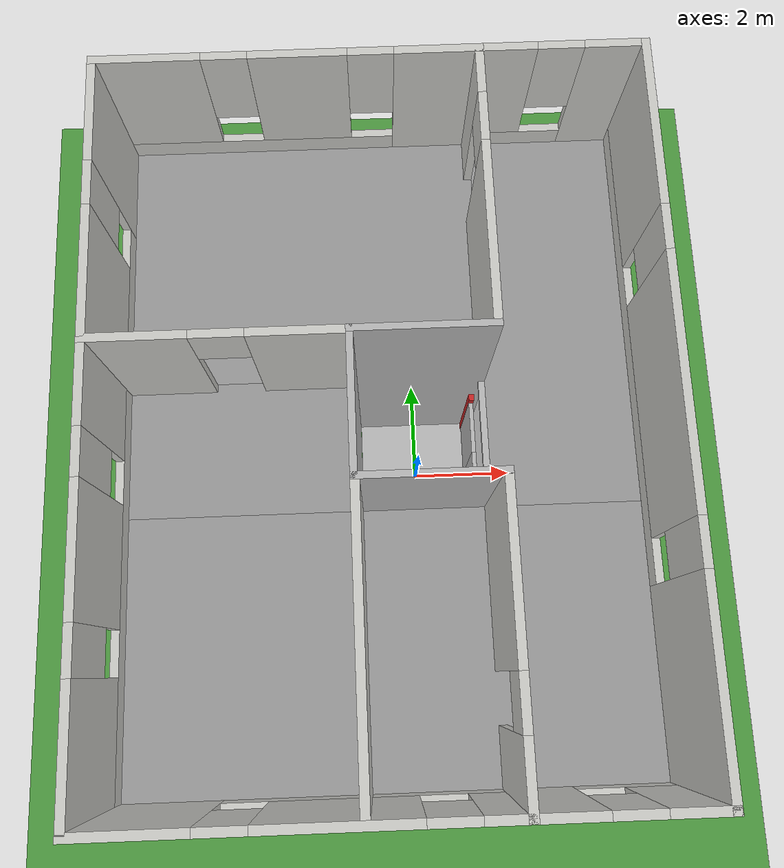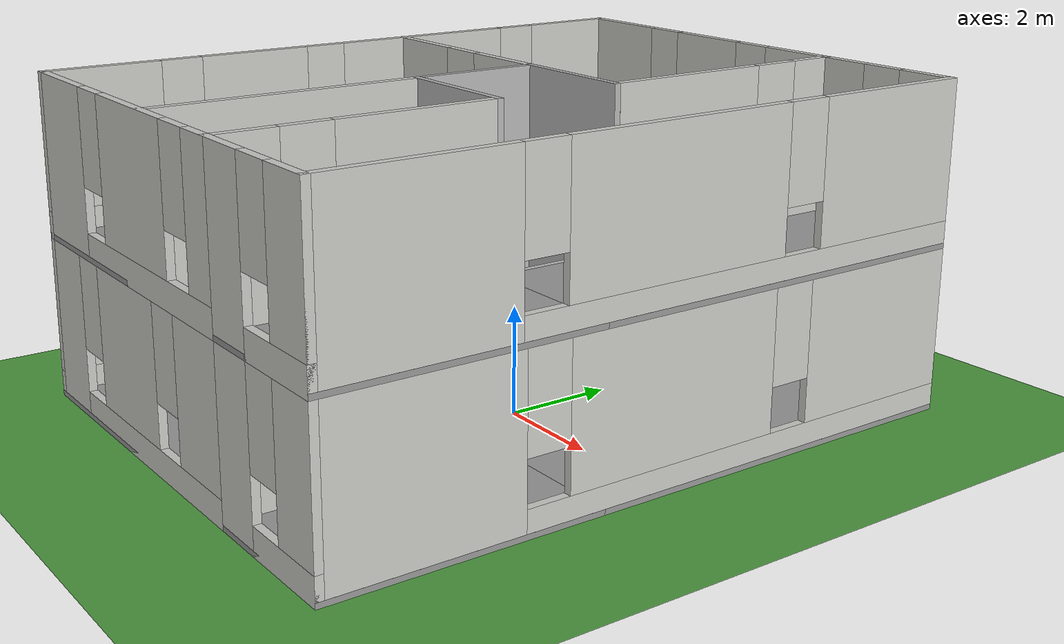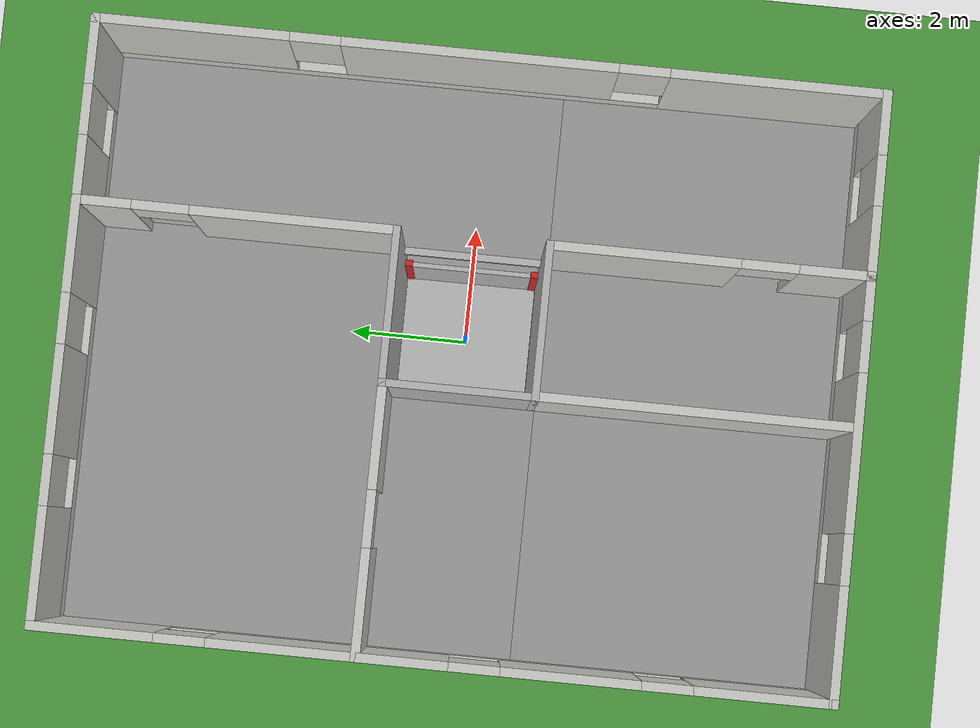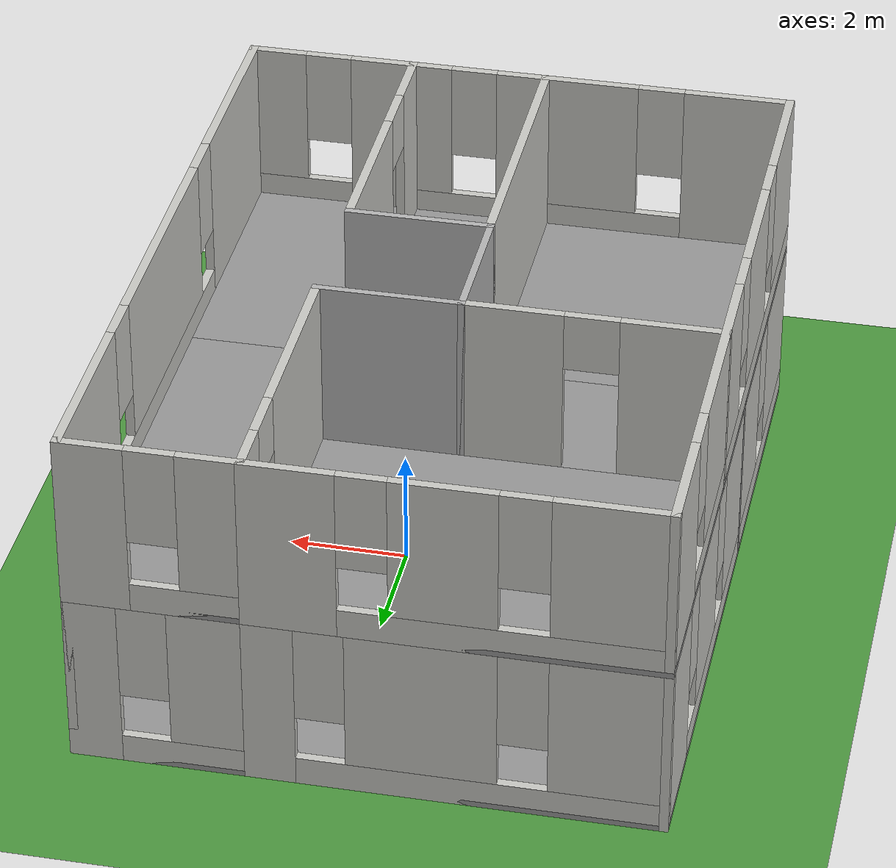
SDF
<?xml version="1.0" ?>
<sdf version="1.5">
  <world name="default">

    <!-- A global light source -->
    <include>
      <uri>model://sun</uri>
    </include>

    <!-- A ground plane -->
    <include>
      <uri>model://ground_plane_gras</uri>
    </include>

    <scene>
      <sky>
        <clouds>
          <speed>12</speed>
        </clouds>
      </sky>
    </scene>

    <include>
      <uri>model://building_with_elevator</uri>
      <pose>-0.6995 0 0 0 0 1.570796</pose>
    </include>

    <!-- World plugin that publishes event messages.
         The topics used in these messages match up with topics used by the
         plugin in the elevator model below.
    -->
    <plugin filename="libSimEventsPlugin.so" name="elevator_event_plugin">
      <!-- Region on the ground floor, in front of the elevator -->
      <region>
        <name>region1</name>
        <volume>
          <min>1.5 -1 0</min>
          <max>2.5 1 1</max>
        </volume>
      </region>

      <!-- Region on the first floor, in front of the elevator -->
      <region>
        <name>region2</name>
        <volume>
          <min>1.5 -1 3</min>
          <max>2.5 1 4</max>
        </volume>
      </region>

      <!-- Event publisher for ground floor-->
      <event>
        <name>region1_event</name>
        <type>occupied</type>
        <region>region1</region>
        <topic>~/elevator</topic>
        <msg_data>0</msg_data>
      </event>

      <!-- Event publisher for first floor-->
      <event>
        <name>region2_event</name>
        <type>occupied</type>
        <region>region2</region>
        <topic>~/elevator</topic>
        <msg_data>1</msg_data>
      </event>
    </plugin>

    <!-- The elevator car -->
    <model name="elevator">
      <pose>0 0 0.05 0 0 0</pose>
      <link name="link">
        <inertial>
          <mass>800</mass>
        </inertial>

        <collision name="floor_collision">
          <geometry>
            <box>
              <size>2.25 2.25 0.1</size>
            </box>
          </geometry>
        </collision>
        <visual name="floor_visual">
          <geometry>
            <box>
              <size>2.25 2.25 0.1</size>
            </box>
          </geometry>
        </visual>

        <!-- wall1_collision is the wall to the right of the door, when
             facing the door -->
        <collision name="wall1_collision">
         <pose>1.0745 1.0625 1.125 0 0 0</pose>
         <geometry>
           <box>
             <size>0.1 0.125 2.25</size>
           </box>
         </geometry>
        </collision>
        <visual name="wall1_visual">
         <pose>1.0745 1.0625 1.125 0 0 0</pose>
         <geometry>
           <box>
             <size>0.1 0.125 2.25</size>
           </box>
         </geometry>
         <material>
           <script>
             <name>Gazebo/Red</name>
           </script>
         </material>
        </visual>

        <!-- wall2_collision is the wall to the left of the door, when
             facing the door -->
        <collision name="wall2_collision">
          <pose>1.0745 -1.0625 1.125 0 0 0</pose>
          <geometry>
            <box>
              <size>0.1 0.125 2.25</size>
            </box>
          </geometry>
        </collision>
        <visual name="wall2_visual">
          <pose>1.0745 -1.0625 1.125 0 0 0</pose>
          <geometry>
            <box>
              <size>0.1 0.125 2.25</size>
            </box>
          </geometry>
          <material>
            <script>
              <name>Gazebo/Red</name>
            </script>
          </material>
        </visual>
      </link>

      <link name="door">
        <pose>1.0745 -0.5 1.06 0 0 0</pose>
        <collision name="collision">
          <geometry>
            <box>
              <size>0.08 1 2.0</size>
            </box>
          </geometry>
        </collision>
        <visual name="visual">
          <geometry>
            <box>
              <size>0.08 1 2.0</size>
            </box>
          </geometry>
        </visual>
      </link>
      <joint name="door" type="revolute">
        <parent>link</parent>
        <child>door</child>
        <pose>0 -0.46 0 3.14159265 0 0</pose>
        <axis>
          <xyz>0 0 1</xyz>
          <limit>
            <lower>0</lower>
            <upper>2</upper>
            <effort>10</effort>
          </limit>

          <dynamics>
            <damping>2</damping>
          </dynamics>
        </axis>
      </joint>

      <link name="door2">
        <pose>1.0745 0.5 1.06 0 0 0</pose>
        <collision name="collision">
          <geometry>
            <box>
              <size>0.08 1 2.0</size>
            </box>
          </geometry>
        </collision>
        <visual name="visual">
          <geometry>
            <box>
              <size>0.08 1 2.0</size>
            </box>
          </geometry>
        </visual>
      </link>
      <joint name="door2" type="revolute">
        <parent>link</parent>
        <child>door2</child>
        <pose>0 0.46 0 0 0 0</pose>
        <axis>
          <xyz>0 0 1</xyz>
          <limit>
            <lower>0</lower>
            <upper>2</upper>
            <effort>10</effort>
          </limit>

          <dynamics>
            <damping>2</damping>
          </dynamics>
        </axis>
      </joint>

      <joint name="lift" type="prismatic">
        <parent>world</parent>
        <child>link</child>
        <axis>
          <xyz>0 0 1</xyz>
          <limit>
            <lower>0</lower>
            <upper>10</upper>
            <effort>100000</effort>
          </limit>

          <dynamics>
            <damping>50</damping>
          </dynamics>
        </axis>
        <physics>
          <ode>
            <implicit_spring_damper>1</implicit_spring_damper>
          </ode>
        </physics>
      </joint>

      <!-- Plugin to control the elevator -->
      <plugin filename="libgazebo_ros_elevator.so" name="elevator_plugin">
        <lift_joint>elevator::lift</lift_joint>
        <door_joint>elevator::door, elevator::door2</door_joint>
        <floor_height>3.0</floor_height>

        <!-- Time the elevator door will stay open in seconds -->
        <door_wait_time>10</door_wait_time>

        <!-- This topic is used to control the elevator -->
        <topic>elevator</topic>

        <door_joint_move_distance>2</door_joint_move_distance>
      </plugin>
    </model>

    <!-- Elevator shaft -->
    <model name="elevator_shaft">
      <static>true</static>
      <link name="link">
        <collision name="shaft_wall1_collision">
          <pose>0 1.19 3 0 0 0</pose>
          <geometry>
            <box>
              <size>2.5 0.12 6</size>
            </box>
          </geometry>
        </collision>
        <visual name="shaft_wall1_visual">
          <pose>0 1.19 3 0 0 0</pose>
          <geometry>
            <box>
              <size>2.5 0.12 6</size>
            </box>
          </geometry>
        </visual>

        <collision name="shaft_wall2_collision">
          <pose>0 -1.19 3 0 0 0</pose>
          <geometry>
            <box>
              <size>2.5 0.12 6</size>
            </box>
          </geometry>
        </collision>
        <visual name="shaft_wall2_visual">
          <pose>0 -1.19 3 0 0 0</pose>
          <geometry>
            <box>
              <size>2.5 0.12 6</size>
            </box>
          </geometry>
        </visual>

        <collision name="shaft_wall3_collision">
          <pose>-1.19 0 3 0 0 0</pose>
          <geometry>
            <box>
              <size>0.12 2.5 6</size>
            </box>
          </geometry>
        </collision>
        <visual name="shaft_wall3_visual">
          <pose>-1.19 0 3 0 0 0</pose>
          <geometry>
            <box>
              <size>0.12 2.5 6</size>
            </box>
          </geometry>
        </visual>

        <collision name="floor0_collision">
          <pose>1.19 0 0.05 0 0 0</pose>
          <geometry>
            <box>
              <size>0.12 2.5 0.1</size>
            </box>
          </geometry>
        </collision>
        <visual name="floor0_visual">
          <pose>1.19 0 0.05 0 0 0</pose>
          <geometry>
            <box>
              <size>0.12 2.5 0.1</size>
            </box>
          </geometry>
        </visual>

        <collision name="floor1_collision">
          <pose>1.19 0 3.05 0 0 0</pose>
          <geometry>
            <box>
              <size>0.12 2.5 0.1</size>
            </box>
          </geometry>
        </collision>
        <visual name="floor1_visual">
          <pose>1.19 0 3.05 0 0 0</pose>
          <geometry>
            <box>
              <size>0.12 2.5 0.1</size>
            </box>
          </geometry>
        </visual>
      </link>
    </model>

  </world>
</sdf>

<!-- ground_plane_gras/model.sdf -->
<sdf version="1.5">
  <model name="ground_plane">
    <static>true</static>
    <link name="link">
      <collision name="collision">
        <geometry>
          <plane>
            <normal>0 0 1</normal>
            <size>100 100</size>
          </plane>
        </geometry>
        <surface>
          <friction>
            <ode>
              <mu>100</mu>
              <mu2>50</mu2>
            </ode>
          </friction>
        </surface>
      </collision>
      <visual name="visual">
        <cast_shadows>false</cast_shadows>
        <geometry>
          <plane>
            <normal>0 0 1</normal>
            <size>100 100</size>
          </plane>
        </geometry>
        <material>
          <script>
            <uri>file://media/materials/scripts/gazebo.material</uri>
            <name>Gazebo/Grass</name>
          </script>
        </material>
      </visual>
    </link>
  </model>
</sdf>

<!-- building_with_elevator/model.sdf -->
<sdf version='1.6'>
  <model name='building_with_elevator'>
    <plugin name="model_transparency" filename="libfloor_transparency_gazebo_model_plugin.so">
      <reference_model>mobile_base</reference_model>
    </plugin>
    <pose frame=''>0 0.6995 0 0 -0 0</pose>
    <link name='Floor_0'>
      <pose frame=''>0 0 0 0 -0 0</pose>
      <visual name='Floor_0_Visual_0'>
        <pose frame=''>-3.7505 0 0.05 0 -0 0</pose>
        <geometry>
          <box>
            <size>5.001 9.60156 0.1</size>
          </box>
        </geometry>
        <material>
          <script>
            <uri>file://media/materials/scripts/gazebo.material</uri>
            <name>Gazebo/Grey</name>
          </script>
          <ambient>1 1 1 1</ambient>
        </material>
      </visual>
      <collision name='Floor_0_Collision_0'>
        <geometry>
          <box>
            <size>5.001 9.60156 0.1</size>
          </box>
        </geometry>
        <pose frame=''>-3.7505 0 0.05 0 -0 0</pose>
      </collision>
      <visual name='Floor_0_Visual_1'>
        <pose frame=''>2.5005 -3.37514 0.05 0 -0 0</pose>
        <geometry>
          <box>
            <size>7.501 2.85128 0.1</size>
          </box>
        </geometry>
        <material>
          <script>
            <uri>file://media/materials/scripts/gazebo.material</uri>
            <name>Gazebo/Grey</name>
          </script>
          <ambient>1 1 1 1</ambient>
        </material>
      </visual>
      <collision name='Floor_0_Collision_1'>
        <geometry>
          <box>
            <size>7.501 2.85128 0.1</size>
          </box>
        </geometry>
        <pose frame=''>2.5005 -3.37514 0.05 0 -0 0</pose>
      </collision>
      <visual name='Floor_0_Visual_2'>
        <pose frame=''>3.7505 1.42564 0.05 0 -0 0</pose>
        <geometry>
          <box>
            <size>5.001 6.75028 0.1</size>
          </box>
        </geometry>
        <material>
          <script>
            <uri>file://media/materials/scripts/gazebo.material</uri>
            <name>Gazebo/Grey</name>
          </script>
          <ambient>1 1 1 1</ambient>
        </material>
      </visual>
      <collision name='Floor_0_Collision_2'>
        <geometry>
          <box>
            <size>5.001 6.75028 0.1</size>
          </box>
        </geometry>
        <pose frame=''>3.7505 1.42564 0.05 0 -0 0</pose>
      </collision>
      <visual name='Floor_0_Visual_3'>
        <pose frame=''>0 2.67564 0.05 0 -0 0</pose>
        <geometry>
          <box>
            <size>2.5 4.25028 0.1</size>
          </box>
        </geometry>
        <material>
          <script>
            <uri>file://media/materials/scripts/gazebo.material</uri>
            <name>Gazebo/Grey</name>
          </script>
          <ambient>1 1 1 1</ambient>
        </material>
      </visual>
      <collision name='Floor_0_Collision_3'>
        <geometry>
          <box>
            <size>2.5 4.25028 0.1</size>
          </box>
        </geometry>
        <pose frame=''>0 2.67564 0.05 0 -0 0</pose>
      </collision>
    </link>
    <link name='Wall_1'>
      <pose frame=''>3.75 -1.8755 0 0 -0 3.14159</pose>
      <visual name='Wall_1_Visual_0'>
        <pose frame=''>-2.22551 0 1.5 0 -0 0</pose>
        <geometry>
          <box>
            <size>0.550979 0.15 3</size>
          </box>
        </geometry>
        <material>
          <script>
            <uri>file://media/materials/scripts/gazebo.material</uri>
            <name>Gazebo/CeilingTiled</name>
          </script>
          <ambient>1 1 1 1</ambient>
        </material>
      </visual>
      <collision name='Wall_1_Collision_0'>
        <geometry>
          <box>
            <size>0.550979 0.15 3</size>
          </box>
        </geometry>
        <pose frame=''>-2.22551 0 1.5 0 -0 0</pose>
      </collision>
      <visual name='Wall_1_Visual_1'>
        <pose frame=''>0.725489 0 1.5 0 -0 0</pose>
        <geometry>
          <box>
            <size>3.55102 0.15 3</size>
          </box>
        </geometry>
        <material>
          <script>
            <uri>file://media/materials/scripts/gazebo.material</uri>
            <name>Gazebo/CeilingTiled</name>
          </script>
          <ambient>1 1 1 1</ambient>
        </material>
      </visual>
      <collision name='Wall_1_Collision_1'>
        <geometry>
          <box>
            <size>3.55102 0.15 3</size>
          </box>
        </geometry>
        <pose frame=''>0.725489 0 1.5 0 -0 0</pose>
      </collision>
      <visual name='Wall_1_Visual_2'>
        <pose frame=''>-1.50002 0 2.5 0 -0 0</pose>
        <geometry>
          <box>
            <size>0.9 0.15 1</size>
          </box>
        </geometry>
        <material>
          <script>
            <uri>file://media/materials/scripts/gazebo.material</uri>
            <name>Gazebo/CeilingTiled</name>
          </script>
          <ambient>1 1 1 1</ambient>
        </material>
      </visual>
      <collision name='Wall_1_Collision_2'>
        <geometry>
          <box>
            <size>0.9 0.15 1</size>
          </box>
        </geometry>
        <pose frame=''>-1.50002 0 2.5 0 -0 0</pose>
      </collision>
    </link>
    <link name='Wall_12'>
      <pose frame=''>6.176 1.4245 0 0 -0 1.5708</pose>
      <visual name='Wall_12_Visual_0'>
        <pose frame=''>-2.95992 0 1.5 0 -0 0</pose>
        <geometry>
          <box>
            <size>0.830166 0.15 3</size>
          </box>
        </geometry>
        <material>
          <script>
            <uri>file://media/materials/scripts/gazebo.material</uri>
            <name>Gazebo/CeilingTiled</name>
          </script>
          <ambient>1 1 1 1</ambient>
        </material>
      </visual>
      <collision name='Wall_12_Collision_0'>
        <geometry>
          <box>
            <size>0.830166 0.15 3</size>
          </box>
        </geometry>
        <pose frame=''>-2.95992 0 1.5 0 -0 0</pose>
      </collision>
      <visual name='Wall_12_Visual_1'>
        <pose frame=''>0.415083 0 0.25 0 -0 0</pose>
        <geometry>
          <box>
            <size>5.91983 0.15 0.5</size>
          </box>
        </geometry>
        <material>
          <script>
            <uri>file://media/materials/scripts/gazebo.material</uri>
            <name>Gazebo/CeilingTiled</name>
          </script>
          <ambient>1 1 1 1</ambient>
        </material>
      </visual>
      <collision name='Wall_12_Collision_1'>
        <geometry>
          <box>
            <size>5.91983 0.15 0.5</size>
          </box>
        </geometry>
        <pose frame=''>0.415083 0 0.25 0 -0 0</pose>
      </collision>
      <visual name='Wall_12_Visual_2'>
        <pose frame=''>-0.543077 0 1.75 0 -0 0</pose>
        <geometry>
          <box>
            <size>2.40351 0.15 2.5</size>
          </box>
        </geometry>
        <material>
          <script>
            <uri>file://media/materials/scripts/gazebo.material</uri>
            <name>Gazebo/CeilingTiled</name>
          </script>
          <ambient>1 1 1 1</ambient>
        </material>
      </visual>
      <collision name='Wall_12_Collision_2'>
        <geometry>
          <box>
            <size>2.40351 0.15 2.5</size>
          </box>
        </geometry>
        <pose frame=''>-0.543077 0 1.75 0 -0 0</pose>
      </collision>
      <visual name='Wall_12_Visual_3'>
        <pose frame=''>2.41684 0 1.75 0 -0 0</pose>
        <geometry>
          <box>
            <size>1.91632 0.15 2.5</size>
          </box>
        </geometry>
        <material>
          <script>
            <uri>file://media/materials/scripts/gazebo.material</uri>
            <name>Gazebo/CeilingTiled</name>
          </script>
          <ambient>1 1 1 1</ambient>
        </material>
      </visual>
      <collision name='Wall_12_Collision_3'>
        <geometry>
          <box>
            <size>1.91632 0.15 2.5</size>
          </box>
        </geometry>
        <pose frame=''>2.41684 0 1.75 0 -0 0</pose>
      </collision>
      <visual name='Wall_12_Visual_4'>
        <pose frame=''>-2.14483 0 2.15 0 -0 0</pose>
        <geometry>
          <box>
            <size>0.8 0.15 1.7</size>
          </box>
        </geometry>
        <material>
          <script>
            <uri>file://media/materials/scripts/gazebo.material</uri>
            <name>Gazebo/CeilingTiled</name>
          </script>
          <ambient>1 1 1 1</ambient>
        </material>
      </visual>
      <collision name='Wall_12_Collision_4'>
        <geometry>
          <box>
            <size>0.8 0.15 1.7</size>
          </box>
        </geometry>
        <pose frame=''>-2.14483 0 2.15 0 -0 0</pose>
      </collision>
      <visual name='Wall_12_Visual_5'>
        <pose frame=''>1.05868 0 2.15 0 -0 0</pose>
        <geometry>
          <box>
            <size>0.8 0.15 1.7</size>
          </box>
        </geometry>
        <material>
          <script>
            <uri>file://media/materials/scripts/gazebo.material</uri>
            <name>Gazebo/CeilingTiled</name>
          </script>
          <ambient>1 1 1 1</ambient>
        </material>
      </visual>
      <collision name='Wall_12_Collision_5'>
        <geometry>
          <box>
            <size>0.8 0.15 1.7</size>
          </box>
        </geometry>
        <pose frame=''>1.05868 0 2.15 0 -0 0</pose>
      </collision>
    </link>
    <link name='Wall_13'>
      <pose frame=''>0 4.7245 0 0 -0 3.14159</pose>
      <visual name='Wall_13_Visual_0'>
        <pose frame=''>-5.3579 0 1.5 0 -0 0</pose>
        <geometry>
          <box>
            <size>1.7862 0.15 3</size>
          </box>
        </geometry>
        <material>
          <script>
            <uri>file://media/materials/scripts/gazebo.material</uri>
            <name>Gazebo/CeilingTiled</name>
          </script>
          <ambient>1 1 1 1</ambient>
        </material>
      </visual>
      <collision name='Wall_13_Collision_0'>
        <geometry>
          <box>
            <size>1.7862 0.15 3</size>
          </box>
        </geometry>
        <pose frame=''>-5.3579 0 1.5 0 -0 0</pose>
      </collision>
      <visual name='Wall_13_Visual_1'>
        <pose frame=''>0.893098 0 0.25 0 -0 0</pose>
        <geometry>
          <box>
            <size>10.7158 0.15 0.5</size>
          </box>
        </geometry>
        <material>
          <script>
            <uri>file://media/materials/scripts/gazebo.material</uri>
            <name>Gazebo/CeilingTiled</name>
          </script>
          <ambient>1 1 1 1</ambient>
        </material>
      </visual>
      <collision name='Wall_13_Collision_1'>
        <geometry>
          <box>
            <size>10.7158 0.15 0.5</size>
          </box>
        </geometry>
        <pose frame=''>0.893098 0 0.25 0 -0 0</pose>
      </collision>
      <visual name='Wall_13_Visual_2'>
        <pose frame=''>-2.64079 0 1.75 0 -0 0</pose>
        <geometry>
          <box>
            <size>2.04803 0.15 2.5</size>
          </box>
        </geometry>
        <material>
          <script>
            <uri>file://media/materials/scripts/gazebo.material</uri>
            <name>Gazebo/CeilingTiled</name>
          </script>
          <ambient>1 1 1 1</ambient>
        </material>
      </visual>
      <collision name='Wall_13_Collision_2'>
        <geometry>
          <box>
            <size>2.04803 0.15 2.5</size>
          </box>
        </geometry>
        <pose frame=''>-2.64079 0 1.75 0 -0 0</pose>
      </collision>
      <visual name='Wall_13_Visual_3'>
        <pose frame=''>1.14669 0 1.75 0 -0 0</pose>
        <geometry>
          <box>
            <size>3.92694 0.15 2.5</size>
          </box>
        </geometry>
        <material>
          <script>
            <uri>file://media/materials/scripts/gazebo.material</uri>
            <name>Gazebo/CeilingTiled</name>
          </script>
          <ambient>1 1 1 1</ambient>
        </material>
      </visual>
      <collision name='Wall_13_Collision_3'>
        <geometry>
          <box>
            <size>3.92694 0.15 2.5</size>
          </box>
        </geometry>
        <pose frame=''>1.14669 0 1.75 0 -0 0</pose>
      </collision>
      <visual name='Wall_13_Visual_4'>
        <pose frame=''>5.08058 0 1.75 0 -0 0</pose>
        <geometry>
          <box>
            <size>2.34084 0.15 2.5</size>
          </box>
        </geometry>
        <material>
          <script>
            <uri>file://media/materials/scripts/gazebo.material</uri>
            <name>Gazebo/CeilingTiled</name>
          </script>
          <ambient>1 1 1 1</ambient>
        </material>
      </visual>
      <collision name='Wall_13_Collision_4'>
        <geometry>
          <box>
            <size>2.34084 0.15 2.5</size>
          </box>
        </geometry>
        <pose frame=''>5.08058 0 1.75 0 -0 0</pose>
      </collision>
      <visual name='Wall_13_Visual_5'>
        <pose frame=''>-4.0648 0 2.15 0 -0 0</pose>
        <geometry>
          <box>
            <size>0.8 0.15 1.7</size>
          </box>
        </geometry>
        <material>
          <script>
            <uri>file://media/materials/scripts/gazebo.material</uri>
            <name>Gazebo/CeilingTiled</name>
          </script>
          <ambient>1 1 1 1</ambient>
        </material>
      </visual>
      <collision name='Wall_13_Collision_5'>
        <geometry>
          <box>
            <size>0.8 0.15 1.7</size>
          </box>
        </geometry>
        <pose frame=''>-4.0648 0 2.15 0 -0 0</pose>
      </collision>
      <visual name='Wall_13_Visual_6'>
        <pose frame=''>-1.21677 0 2.15 0 -0 0</pose>
        <geometry>
          <box>
            <size>0.8 0.15 1.7</size>
          </box>
        </geometry>
        <material>
          <script>
            <uri>file://media/materials/scripts/gazebo.material</uri>
            <name>Gazebo/CeilingTiled</name>
          </script>
          <ambient>1 1 1 1</ambient>
        </material>
      </visual>
      <collision name='Wall_13_Collision_6'>
        <geometry>
          <box>
            <size>0.8 0.15 1.7</size>
          </box>
        </geometry>
        <pose frame=''>-1.21677 0 2.15 0 -0 0</pose>
      </collision>
      <visual name='Wall_13_Visual_7'>
        <pose frame=''>3.51016 0 2.15 0 -0 0</pose>
        <geometry>
          <box>
            <size>0.8 0.15 1.7</size>
          </box>
        </geometry>
        <material>
          <script>
            <uri>file://media/materials/scripts/gazebo.material</uri>
            <name>Gazebo/CeilingTiled</name>
          </script>
          <ambient>1 1 1 1</ambient>
        </material>
      </visual>
      <collision name='Wall_13_Collision_7'>
        <geometry>
          <box>
            <size>0.8 0.15 1.7</size>
          </box>
        </geometry>
        <pose frame=''>3.51016 0 2.15 0 -0 0</pose>
      </collision>
    </link>
    <link name='Wall_14'>
      <pose frame=''>-6.176 1.4245 0 0 0 -1.5708</pose>
      <visual name='Wall_14_Visual_0'>
        <pose frame=''>-2.68372 0 1.5 0 -0 0</pose>
        <geometry>
          <box>
            <size>1.38232 0.15 3</size>
          </box>
        </geometry>
        <material>
          <script>
            <uri>file://media/materials/scripts/gazebo.material</uri>
            <name>Gazebo/CeilingTiled</name>
          </script>
          <ambient>1 1 1 1</ambient>
        </material>
      </visual>
      <collision name='Wall_14_Collision_0'>
        <geometry>
          <box>
            <size>1.38232 0.15 3</size>
          </box>
        </geometry>
        <pose frame=''>-2.68372 0 1.5 0 -0 0</pose>
      </collision>
      <visual name='Wall_14_Visual_1'>
        <pose frame=''>0.691162 0 0.25 0 -0 0</pose>
        <geometry>
          <box>
            <size>5.36744 0.15 0.5</size>
          </box>
        </geometry>
        <material>
          <script>
            <uri>file://media/materials/scripts/gazebo.material</uri>
            <name>Gazebo/CeilingTiled</name>
          </script>
          <ambient>1 1 1 1</ambient>
        </material>
      </visual>
      <collision name='Wall_14_Collision_1'>
        <geometry>
          <box>
            <size>5.36744 0.15 0.5</size>
          </box>
        </geometry>
        <pose frame=''>0.691162 0 0.25 0 -0 0</pose>
      </collision>
      <visual name='Wall_14_Visual_2'>
        <pose frame=''>-0.040189 0 1.75 0 -0 0</pose>
        <geometry>
          <box>
            <size>2.30474 0.15 2.5</size>
          </box>
        </geometry>
        <material>
          <script>
            <uri>file://media/materials/scripts/gazebo.material</uri>
            <name>Gazebo/CeilingTiled</name>
          </script>
          <ambient>1 1 1 1</ambient>
        </material>
      </visual>
      <collision name='Wall_14_Collision_2'>
        <geometry>
          <box>
            <size>2.30474 0.15 2.5</size>
          </box>
        </geometry>
        <pose frame=''>-0.040189 0 1.75 0 -0 0</pose>
      </collision>
      <visual name='Wall_14_Visual_3'>
        <pose frame=''>2.64353 0 1.75 0 -0 0</pose>
        <geometry>
          <box>
            <size>1.4627 0.15 2.5</size>
          </box>
        </geometry>
        <material>
          <script>
            <uri>file://media/materials/scripts/gazebo.material</uri>
            <name>Gazebo/CeilingTiled</name>
          </script>
          <ambient>1 1 1 1</ambient>
        </material>
      </visual>
      <collision name='Wall_14_Collision_3'>
        <geometry>
          <box>
            <size>1.4627 0.15 2.5</size>
          </box>
        </geometry>
        <pose frame=''>2.64353 0 1.75 0 -0 0</pose>
      </collision>
      <visual name='Wall_14_Visual_4'>
        <pose frame=''>-1.59256 0 2.15 0 -0 0</pose>
        <geometry>
          <box>
            <size>0.8 0.15 1.7</size>
          </box>
        </geometry>
        <material>
          <script>
            <uri>file://media/materials/scripts/gazebo.material</uri>
            <name>Gazebo/CeilingTiled</name>
          </script>
          <ambient>1 1 1 1</ambient>
        </material>
      </visual>
      <collision name='Wall_14_Collision_4'>
        <geometry>
          <box>
            <size>0.8 0.15 1.7</size>
          </box>
        </geometry>
        <pose frame=''>-1.59256 0 2.15 0 -0 0</pose>
      </collision>
      <visual name='Wall_14_Visual_5'>
        <pose frame=''>1.51218 0 2.15 0 -0 0</pose>
        <geometry>
          <box>
            <size>0.8 0.15 1.7</size>
          </box>
        </geometry>
        <material>
          <script>
            <uri>file://media/materials/scripts/gazebo.material</uri>
            <name>Gazebo/CeilingTiled</name>
          </script>
          <ambient>1 1 1 1</ambient>
        </material>
      </visual>
      <collision name='Wall_14_Collision_5'>
        <geometry>
          <box>
            <size>0.8 0.15 1.7</size>
          </box>
        </geometry>
        <pose frame=''>1.51218 0 2.15 0 -0 0</pose>
      </collision>
    </link>
    <link name='Wall_16'>
      <pose frame=''>-1.175 2.6755 0 0 -0 1.5708</pose>
      <visual name='Wall_16_Visual_0'>
        <pose frame=''>-1.3834 0 1.5 0 -0 0</pose>
        <geometry>
          <box>
            <size>1.48321 0.15 3</size>
          </box>
        </geometry>
        <material>
          <script>
            <uri>file://media/materials/scripts/gazebo.material</uri>
            <name>Gazebo/Grey</name>
          </script>
          <ambient>1 1 1 1</ambient>
        </material>
      </visual>
      <collision name='Wall_16_Collision_0'>
        <geometry>
          <box>
            <size>1.48321 0.15 3</size>
          </box>
        </geometry>
        <pose frame=''>-1.3834 0 1.5 0 -0 0</pose>
      </collision>
      <visual name='Wall_16_Visual_1'>
        <pose frame=''>1.1916 0 1.5 0 -0 0</pose>
        <geometry>
          <box>
            <size>1.86679 0.15 3</size>
          </box>
        </geometry>
        <material>
          <script>
            <uri>file://media/materials/scripts/gazebo.material</uri>
            <name>Gazebo/Grey</name>
          </script>
          <ambient>1 1 1 1</ambient>
        </material>
      </visual>
      <collision name='Wall_16_Collision_1'>
        <geometry>
          <box>
            <size>1.86679 0.15 3</size>
          </box>
        </geometry>
        <pose frame=''>1.1916 0 1.5 0 -0 0</pose>
      </collision>
      <visual name='Wall_16_Visual_2'>
        <pose frame=''>-0.191795 0 2.5 0 -0 0</pose>
        <geometry>
          <box>
            <size>0.9 0.15 1</size>
          </box>
        </geometry>
        <material>
          <script>
            <uri>file://media/materials/scripts/gazebo.material</uri>
            <name>Gazebo/Grey</name>
          </script>
          <ambient>1 1 1 1</ambient>
        </material>
      </visual>
      <collision name='Wall_16_Collision_2'>
        <geometry>
          <box>
            <size>0.9 0.15 1</size>
          </box>
        </geometry>
        <pose frame=''>-0.191795 0 2.5 0 -0 0</pose>
      </collision>
    </link>
    <link name='Wall_18'>
      <collision name='Wall_18_Collision'>
        <geometry>
          <box>
            <size>5 0.15 3</size>
          </box>
        </geometry>
        <pose frame=''>0 0 1.5 0 -0 0</pose>
      </collision>
      <visual name='Wall_18_Visual'>
        <pose frame=''>0 0 1.5 0 -0 0</pose>
        <geometry>
          <box>
            <size>5 0.15 3</size>
          </box>
        </geometry>
        <material>
          <script>
            <uri>file://media/materials/scripts/gazebo.material</uri>
            <name>Gazebo/CeilingTiled</name>
          </script>
          <ambient>1 1 1 1</ambient>
        </material>
      </visual>
      <pose frame=''>3.748 0.4825 0 0 -0 0</pose>
    </link>
    <link name='Floor_1'>
      <pose frame=''>0 0 3 0 -0 0</pose>
      <visual name='Floor_1_Visual_0'>
        <pose frame=''>-3.7505 0 0.05 0 -0 0</pose>
        <geometry>
          <box>
            <size>5.001 9.60156 0.1</size>
          </box>
        </geometry>
        <material>
          <script>
            <uri>file://media/materials/scripts/gazebo.material</uri>
            <name>Gazebo/Grey</name>
          </script>
          <ambient>1 1 1 1</ambient>
        </material>
      </visual>
      <collision name='Floor_1_Collision_0'>
        <geometry>
          <box>
            <size>5.001 9.60156 0.1</size>
          </box>
        </geometry>
        <pose frame=''>-3.7505 0 0.05 0 -0 0</pose>
      </collision>
      <visual name='Floor_1_Visual_1'>
        <pose frame=''>2.5005 -3.37514 0.05 0 -0 0</pose>
        <geometry>
          <box>
            <size>7.501 2.85128 0.1</size>
          </box>
        </geometry>
        <material>
          <script>
            <uri>file://media/materials/scripts/gazebo.material</uri>
            <name>Gazebo/Grey</name>
          </script>
          <ambient>1 1 1 1</ambient>
        </material>
      </visual>
      <collision name='Floor_1_Collision_1'>
        <geometry>
          <box>
            <size>7.501 2.85128 0.1</size>
          </box>
        </geometry>
        <pose frame=''>2.5005 -3.37514 0.05 0 -0 0</pose>
      </collision>
      <visual name='Floor_1_Visual_2'>
        <pose frame=''>3.7505 1.42564 0.05 0 -0 0</pose>
        <geometry>
          <box>
            <size>5.001 6.75028 0.1</size>
          </box>
        </geometry>
        <material>
          <script>
            <uri>file://media/materials/scripts/gazebo.material</uri>
            <name>Gazebo/Grey</name>
          </script>
          <ambient>1 1 1 1</ambient>
        </material>
      </visual>
      <collision name='Floor_1_Collision_2'>
        <geometry>
          <box>
            <size>5.001 6.75028 0.1</size>
          </box>
        </geometry>
        <pose frame=''>3.7505 1.42564 0.05 0 -0 0</pose>
      </collision>
      <visual name='Floor_1_Visual_3'>
        <pose frame=''>0 2.67564 0.05 0 -0 0</pose>
        <geometry>
          <box>
            <size>2.5 4.25028 0.1</size>
          </box>
        </geometry>
        <material>
          <script>
            <uri>file://media/materials/scripts/gazebo.material</uri>
            <name>Gazebo/Grey</name>
          </script>
          <ambient>1 1 1 1</ambient>
        </material>
      </visual>
      <collision name='Floor_1_Collision_3'>
        <geometry>
          <box>
            <size>2.5 4.25028 0.1</size>
          </box>
        </geometry>
        <pose frame=''>0 2.67564 0.05 0 -0 0</pose>
      </collision>
    </link>
    <link name='Wall_21'>
      <pose frame=''>3.75 -1.8755 3 0 -0 3.14159</pose>
      <visual name='Wall_21_Visual_0'>
        <pose frame=''>-2.03547 0 1.5 0 -0 0</pose>
        <geometry>
          <box>
            <size>0.931051 0.15 3</size>
          </box>
        </geometry>
        <material>
          <script>
            <uri>file://media/materials/scripts/gazebo.material</uri>
            <name>Gazebo/CeilingTiled</name>
          </script>
          <ambient>1 1 1 1</ambient>
        </material>
      </visual>
      <collision name='Wall_21_Collision_0'>
        <geometry>
          <box>
            <size>0.931051 0.15 3</size>
          </box>
        </geometry>
        <pose frame=''>-2.03547 0 1.5 0 -0 0</pose>
      </collision>
      <visual name='Wall_21_Visual_1'>
        <pose frame=''>0.915525 0 1.5 0 -0 0</pose>
        <geometry>
          <box>
            <size>3.17095 0.15 3</size>
          </box>
        </geometry>
        <material>
          <script>
            <uri>file://media/materials/scripts/gazebo.material</uri>
            <name>Gazebo/CeilingTiled</name>
          </script>
          <ambient>1 1 1 1</ambient>
        </material>
      </visual>
      <collision name='Wall_21_Collision_1'>
        <geometry>
          <box>
            <size>3.17095 0.15 3</size>
          </box>
        </geometry>
        <pose frame=''>0.915525 0 1.5 0 -0 0</pose>
      </collision>
      <visual name='Wall_21_Visual_2'>
        <pose frame=''>-1.11995 0 2.5 0 -0 0</pose>
        <geometry>
          <box>
            <size>0.9 0.15 1</size>
          </box>
        </geometry>
        <material>
          <script>
            <uri>file://media/materials/scripts/gazebo.material</uri>
            <name>Gazebo/CeilingTiled</name>
          </script>
          <ambient>1 1 1 1</ambient>
        </material>
      </visual>
      <collision name='Wall_21_Collision_2'>
        <geometry>
          <box>
            <size>0.9 0.15 1</size>
          </box>
        </geometry>
        <pose frame=''>-1.11995 0 2.5 0 -0 0</pose>
      </collision>
    </link>
    <link name='Wall_22'>
      <pose frame=''>-3.751 -1.8755 3 0 -0 3.14159</pose>
      <visual name='Wall_22_Visual_0'>
        <pose frame=''>-1.04559 0 1.5 0 -0 0</pose>
        <geometry>
          <box>
            <size>2.90882 0.15 3</size>
          </box>
        </geometry>
        <material>
          <script>
            <uri>file://media/materials/scripts/gazebo.material</uri>
            <name>Gazebo/CeilingTiled</name>
          </script>
          <ambient>1 1 1 1</ambient>
        </material>
      </visual>
      <collision name='Wall_22_Collision_0'>
        <geometry>
          <box>
            <size>2.90882 0.15 3</size>
          </box>
        </geometry>
        <pose frame=''>-1.04559 0 1.5 0 -0 0</pose>
      </collision>
      <visual name='Wall_22_Visual_1'>
        <pose frame=''>1.90441 0 1.5 0 -0 0</pose>
        <geometry>
          <box>
            <size>1.19118 0.15 3</size>
          </box>
        </geometry>
        <material>
          <script>
            <uri>file://media/materials/scripts/gazebo.material</uri>
            <name>Gazebo/CeilingTiled</name>
          </script>
          <ambient>1 1 1 1</ambient>
        </material>
      </visual>
      <collision name='Wall_22_Collision_1'>
        <geometry>
          <box>
            <size>1.19118 0.15 3</size>
          </box>
        </geometry>
        <pose frame=''>1.90441 0 1.5 0 -0 0</pose>
      </collision>
      <visual name='Wall_22_Visual_2'>
        <pose frame=''>0.858818 0 2.5 0 -0 0</pose>
        <geometry>
          <box>
            <size>0.9 0.15 1</size>
          </box>
        </geometry>
        <material>
          <script>
            <uri>file://media/materials/scripts/gazebo.material</uri>
            <name>Gazebo/CeilingTiled</name>
          </script>
          <ambient>1 1 1 1</ambient>
        </material>
      </visual>
      <collision name='Wall_22_Collision_2'>
        <geometry>
          <box>
            <size>0.9 0.15 1</size>
          </box>
        </geometry>
        <pose frame=''>0.858818 0 2.5 0 -0 0</pose>
      </collision>
    </link>
    <link name='Wall_23'>
      <pose frame=''>-6.176 -3.3005 3 0 0 -1.5708</pose>
      <visual name='Wall_23_Visual_0'>
        <pose frame=''>-0.914344 0 1.5 0 -0 0</pose>
        <geometry>
          <box>
            <size>1.17131 0.15 3</size>
          </box>
        </geometry>
        <material>
          <script>
            <uri>file://media/materials/scripts/gazebo.material</uri>
            <name>Gazebo/CeilingTiled</name>
          </script>
          <ambient>1 1 1 1</ambient>
        </material>
      </visual>
      <collision name='Wall_23_Collision_0'>
        <geometry>
          <box>
            <size>1.17131 0.15 3</size>
          </box>
        </geometry>
        <pose frame=''>-0.914344 0 1.5 0 -0 0</pose>
      </collision>
      <visual name='Wall_23_Visual_1'>
        <pose frame=''>0.585656 0 0.25 0 -0 0</pose>
        <geometry>
          <box>
            <size>1.82869 0.15 0.5</size>
          </box>
        </geometry>
        <material>
          <script>
            <uri>file://media/materials/scripts/gazebo.material</uri>
            <name>Gazebo/CeilingTiled</name>
          </script>
          <ambient>1 1 1 1</ambient>
        </material>
      </visual>
      <collision name='Wall_23_Collision_1'>
        <geometry>
          <box>
            <size>1.82869 0.15 0.5</size>
          </box>
        </geometry>
        <pose frame=''>0.585656 0 0.25 0 -0 0</pose>
      </collision>
      <visual name='Wall_23_Visual_2'>
        <pose frame=''>0.985656 0 1.75 0 -0 0</pose>
        <geometry>
          <box>
            <size>1.02869 0.15 2.5</size>
          </box>
        </geometry>
        <material>
          <script>
            <uri>file://media/materials/scripts/gazebo.material</uri>
            <name>Gazebo/CeilingTiled</name>
          </script>
          <ambient>1 1 1 1</ambient>
        </material>
      </visual>
      <collision name='Wall_23_Collision_2'>
        <geometry>
          <box>
            <size>1.02869 0.15 2.5</size>
          </box>
        </geometry>
        <pose frame=''>0.985656 0 1.75 0 -0 0</pose>
      </collision>
      <visual name='Wall_23_Visual_3'>
        <pose frame=''>0.071312 0 2.15 0 -0 0</pose>
        <geometry>
          <box>
            <size>0.8 0.15 1.7</size>
          </box>
        </geometry>
        <material>
          <script>
            <uri>file://media/materials/scripts/gazebo.material</uri>
            <name>Gazebo/CeilingTiled</name>
          </script>
          <ambient>1 1 1 1</ambient>
        </material>
      </visual>
      <collision name='Wall_23_Collision_3'>
        <geometry>
          <box>
            <size>0.8 0.15 1.7</size>
          </box>
        </geometry>
        <pose frame=''>0.071312 0 2.15 0 -0 0</pose>
      </collision>
    </link>
    <link name='Wall_24'>
      <pose frame=''>0 -4.7255 3 0 -0 0</pose>
      <visual name='Wall_24_Visual_0'>
        <pose frame=''>-4.52369 0 1.5 0 -0 0</pose>
        <geometry>
          <box>
            <size>3.45462 0.15 3</size>
          </box>
        </geometry>
        <material>
          <script>
            <uri>file://media/materials/scripts/gazebo.material</uri>
            <name>Gazebo/CeilingTiled</name>
          </script>
          <ambient>1 1 1 1</ambient>
        </material>
      </visual>
      <collision name='Wall_24_Collision_0'>
        <geometry>
          <box>
            <size>3.45462 0.15 3</size>
          </box>
        </geometry>
        <pose frame=''>-4.52369 0 1.5 0 -0 0</pose>
      </collision>
      <visual name='Wall_24_Visual_1'>
        <pose frame=''>1.72731 0 0.25 0 -0 0</pose>
        <geometry>
          <box>
            <size>9.04738 0.15 0.5</size>
          </box>
        </geometry>
        <material>
          <script>
            <uri>file://media/materials/scripts/gazebo.material</uri>
            <name>Gazebo/CeilingTiled</name>
          </script>
          <ambient>1 1 1 1</ambient>
        </material>
      </visual>
      <collision name='Wall_24_Collision_1'>
        <geometry>
          <box>
            <size>9.04738 0.15 0.5</size>
          </box>
        </geometry>
        <pose frame=''>1.72731 0 0.25 0 -0 0</pose>
      </collision>
      <visual name='Wall_24_Visual_2'>
        <pose frame=''>0.174782 0 1.75 0 -0 0</pose>
        <geometry>
          <box>
            <size>4.34233 0.15 2.5</size>
          </box>
        </geometry>
        <material>
          <script>
            <uri>file://media/materials/scripts/gazebo.material</uri>
            <name>Gazebo/CeilingTiled</name>
          </script>
          <ambient>1 1 1 1</ambient>
        </material>
      </visual>
      <collision name='Wall_24_Collision_2'>
        <geometry>
          <box>
            <size>4.34233 0.15 2.5</size>
          </box>
        </geometry>
        <pose frame=''>0.174782 0 1.75 0 -0 0</pose>
      </collision>
      <visual name='Wall_24_Visual_3'>
        <pose frame=''>4.69847 0 1.75 0 -0 0</pose>
        <geometry>
          <box>
            <size>3.10506 0.15 2.5</size>
          </box>
        </geometry>
        <material>
          <script>
            <uri>file://media/materials/scripts/gazebo.material</uri>
            <name>Gazebo/CeilingTiled</name>
          </script>
          <ambient>1 1 1 1</ambient>
        </material>
      </visual>
      <collision name='Wall_24_Collision_3'>
        <geometry>
          <box>
            <size>3.10506 0.15 2.5</size>
          </box>
        </geometry>
        <pose frame=''>4.69847 0 1.75 0 -0 0</pose>
      </collision>
      <visual name='Wall_24_Visual_4'>
        <pose frame=''>-2.39638 0 2.15 0 -0 0</pose>
        <geometry>
          <box>
            <size>0.8 0.15 1.7</size>
          </box>
        </geometry>
        <material>
          <script>
            <uri>file://media/materials/scripts/gazebo.material</uri>
            <name>Gazebo/CeilingTiled</name>
          </script>
          <ambient>1 1 1 1</ambient>
        </material>
      </visual>
      <collision name='Wall_24_Collision_4'>
        <geometry>
          <box>
            <size>0.8 0.15 1.7</size>
          </box>
        </geometry>
        <pose frame=''>-2.39638 0 2.15 0 -0 0</pose>
      </collision>
      <visual name='Wall_24_Visual_5'>
        <pose frame=''>2.74594 0 2.15 0 -0 0</pose>
        <geometry>
          <box>
            <size>0.8 0.15 1.7</size>
          </box>
        </geometry>
        <material>
          <script>
            <uri>file://media/materials/scripts/gazebo.material</uri>
            <name>Gazebo/CeilingTiled</name>
          </script>
          <ambient>1 1 1 1</ambient>
        </material>
      </visual>
      <collision name='Wall_24_Collision_5'>
        <geometry>
          <box>
            <size>0.8 0.15 1.7</size>
          </box>
        </geometry>
        <pose frame=''>2.74594 0 2.15 0 -0 0</pose>
      </collision>
    </link>
    <link name='Wall_25'>
      <pose frame=''>6.176 -3.3005 3 0 -0 1.5708</pose>
      <visual name='Wall_25_Visual_0'>
        <pose frame=''>-0.94094 0 1.5 0 -0 0</pose>
        <geometry>
          <box>
            <size>1.11812 0.15 3</size>
          </box>
        </geometry>
        <material>
          <script>
            <uri>file://media/materials/scripts/gazebo.material</uri>
            <name>Gazebo/CeilingTiled</name>
          </script>
          <ambient>1 1 1 1</ambient>
        </material>
      </visual>
      <collision name='Wall_25_Collision_0'>
        <geometry>
          <box>
            <size>1.11812 0.15 3</size>
          </box>
        </geometry>
        <pose frame=''>-0.94094 0 1.5 0 -0 0</pose>
      </collision>
      <visual name='Wall_25_Visual_1'>
        <pose frame=''>0.55906 0 0.25 0 -0 0</pose>
        <geometry>
          <box>
            <size>1.88188 0.15 0.5</size>
          </box>
        </geometry>
        <material>
          <script>
            <uri>file://media/materials/scripts/gazebo.material</uri>
            <name>Gazebo/CeilingTiled</name>
          </script>
          <ambient>1 1 1 1</ambient>
        </material>
      </visual>
      <collision name='Wall_25_Collision_1'>
        <geometry>
          <box>
            <size>1.88188 0.15 0.5</size>
          </box>
        </geometry>
        <pose frame=''>0.55906 0 0.25 0 -0 0</pose>
      </collision>
      <visual name='Wall_25_Visual_2'>
        <pose frame=''>0.95906 0 1.75 0 -0 0</pose>
        <geometry>
          <box>
            <size>1.08188 0.15 2.5</size>
          </box>
        </geometry>
        <material>
          <script>
            <uri>file://media/materials/scripts/gazebo.material</uri>
            <name>Gazebo/CeilingTiled</name>
          </script>
          <ambient>1 1 1 1</ambient>
        </material>
      </visual>
      <collision name='Wall_25_Collision_2'>
        <geometry>
          <box>
            <size>1.08188 0.15 2.5</size>
          </box>
        </geometry>
        <pose frame=''>0.95906 0 1.75 0 -0 0</pose>
      </collision>
      <visual name='Wall_25_Visual_3'>
        <pose frame=''>0.018119 0 2.15 0 -0 0</pose>
        <geometry>
          <box>
            <size>0.8 0.15 1.7</size>
          </box>
        </geometry>
        <material>
          <script>
            <uri>file://media/materials/scripts/gazebo.material</uri>
            <name>Gazebo/CeilingTiled</name>
          </script>
          <ambient>1 1 1 1</ambient>
        </material>
      </visual>
      <collision name='Wall_25_Collision_3'>
        <geometry>
          <box>
            <size>0.8 0.15 1.7</size>
          </box>
        </geometry>
        <pose frame=''>0.018119 0 2.15 0 -0 0</pose>
      </collision>
    </link>
    <link name='Wall_26'>
      <pose frame=''>6.176 1.4245 3 0 -0 1.5708</pose>
      <visual name='Wall_26_Visual_0'>
        <pose frame=''>-2.60881 0 1.5 0 -0 0</pose>
        <geometry>
          <box>
            <size>1.53238 0.15 3</size>
          </box>
        </geometry>
        <material>
          <script>
            <uri>file://media/materials/scripts/gazebo.material</uri>
            <name>Gazebo/CeilingTiled</name>
          </script>
          <ambient>1 1 1 1</ambient>
        </material>
      </visual>
      <collision name='Wall_26_Collision_0'>
        <geometry>
          <box>
            <size>1.53238 0.15 3</size>
          </box>
        </geometry>
        <pose frame=''>-2.60881 0 1.5 0 -0 0</pose>
      </collision>
      <visual name='Wall_26_Visual_1'>
        <pose frame=''>0.766189 0 0.25 0 -0 0</pose>
        <geometry>
          <box>
            <size>5.21762 0.15 0.5</size>
          </box>
        </geometry>
        <material>
          <script>
            <uri>file://media/materials/scripts/gazebo.material</uri>
            <name>Gazebo/CeilingTiled</name>
          </script>
          <ambient>1 1 1 1</ambient>
        </material>
      </visual>
      <collision name='Wall_26_Collision_1'>
        <geometry>
          <box>
            <size>5.21762 0.15 0.5</size>
          </box>
        </geometry>
        <pose frame=''>0.766189 0 0.25 0 -0 0</pose>
      </collision>
      <visual name='Wall_26_Visual_2'>
        <pose frame=''>-0.190577 0 1.75 0 -0 0</pose>
        <geometry>
          <box>
            <size>1.70409 0.15 2.5</size>
          </box>
        </geometry>
        <material>
          <script>
            <uri>file://media/materials/scripts/gazebo.material</uri>
            <name>Gazebo/CeilingTiled</name>
          </script>
          <ambient>1 1 1 1</ambient>
        </material>
      </visual>
      <collision name='Wall_26_Collision_2'>
        <geometry>
          <box>
            <size>1.70409 0.15 2.5</size>
          </box>
        </geometry>
        <pose frame=''>-0.190577 0 1.75 0 -0 0</pose>
      </collision>
      <visual name='Wall_26_Visual_3'>
        <pose frame=''>2.41823 0 1.75 0 -0 0</pose>
        <geometry>
          <box>
            <size>1.91353 0.15 2.5</size>
          </box>
        </geometry>
        <material>
          <script>
            <uri>file://media/materials/scripts/gazebo.material</uri>
            <name>Gazebo/CeilingTiled</name>
          </script>
          <ambient>1 1 1 1</ambient>
        </material>
      </visual>
      <collision name='Wall_26_Collision_3'>
        <geometry>
          <box>
            <size>1.91353 0.15 2.5</size>
          </box>
        </geometry>
        <pose frame=''>2.41823 0 1.75 0 -0 0</pose>
      </collision>
      <visual name='Wall_26_Visual_4'>
        <pose frame=''>-1.44262 0 2.15 0 -0 0</pose>
        <geometry>
          <box>
            <size>0.8 0.15 1.7</size>
          </box>
        </geometry>
        <material>
          <script>
            <uri>file://media/materials/scripts/gazebo.material</uri>
            <name>Gazebo/CeilingTiled</name>
          </script>
          <ambient>1 1 1 1</ambient>
        </material>
      </visual>
      <collision name='Wall_26_Collision_4'>
        <geometry>
          <box>
            <size>0.8 0.15 1.7</size>
          </box>
        </geometry>
        <pose frame=''>-1.44262 0 2.15 0 -0 0</pose>
      </collision>
      <visual name='Wall_26_Visual_5'>
        <pose frame=''>1.06147 0 2.15 0 -0 0</pose>
        <geometry>
          <box>
            <size>0.8 0.15 1.7</size>
          </box>
        </geometry>
        <material>
          <script>
            <uri>file://media/materials/scripts/gazebo.material</uri>
            <name>Gazebo/CeilingTiled</name>
          </script>
          <ambient>1 1 1 1</ambient>
        </material>
      </visual>
      <collision name='Wall_26_Collision_5'>
        <geometry>
          <box>
            <size>0.8 0.15 1.7</size>
          </box>
        </geometry>
        <pose frame=''>1.06147 0 2.15 0 -0 0</pose>
      </collision>
    </link>
    <link name='Wall_27'>
      <pose frame=''>0 4.7245 3 0 -0 3.14159</pose>
      <visual name='Wall_27_Visual_0'>
        <pose frame=''>-5.2686 0 1.5 0 -0 0</pose>
        <geometry>
          <box>
            <size>1.9648 0.15 3</size>
          </box>
        </geometry>
        <material>
          <script>
            <uri>file://media/materials/scripts/gazebo.material</uri>
            <name>Gazebo/CeilingTiled</name>
          </script>
          <ambient>1 1 1 1</ambient>
        </material>
      </visual>
      <collision name='Wall_27_Collision_0'>
        <geometry>
          <box>
            <size>1.9648 0.15 3</size>
          </box>
        </geometry>
        <pose frame=''>-5.2686 0 1.5 0 -0 0</pose>
      </collision>
      <visual name='Wall_27_Visual_1'>
        <pose frame=''>0.9824 0 0.25 0 -0 0</pose>
        <geometry>
          <box>
            <size>10.5372 0.15 0.5</size>
          </box>
        </geometry>
        <material>
          <script>
            <uri>file://media/materials/scripts/gazebo.material</uri>
            <name>Gazebo/CeilingTiled</name>
          </script>
          <ambient>1 1 1 1</ambient>
        </material>
      </visual>
      <collision name='Wall_27_Collision_1'>
        <geometry>
          <box>
            <size>10.5372 0.15 0.5</size>
          </box>
        </geometry>
        <pose frame=''>0.9824 0 0.25 0 -0 0</pose>
      </collision>
      <visual name='Wall_27_Visual_2'>
        <pose frame=''>-1.61687 0 1.75 0 -0 0</pose>
        <geometry>
          <box>
            <size>3.73866 0.15 2.5</size>
          </box>
        </geometry>
        <material>
          <script>
            <uri>file://media/materials/scripts/gazebo.material</uri>
            <name>Gazebo/CeilingTiled</name>
          </script>
          <ambient>1 1 1 1</ambient>
        </material>
      </visual>
      <collision name='Wall_27_Collision_2'>
        <geometry>
          <box>
            <size>3.73866 0.15 2.5</size>
          </box>
        </geometry>
        <pose frame=''>-1.61687 0 1.75 0 -0 0</pose>
      </collision>
      <visual name='Wall_27_Visual_3'>
        <pose frame=''>2.13926 0 1.75 0 -0 0</pose>
        <geometry>
          <box>
            <size>2.17361 0.15 2.5</size>
          </box>
        </geometry>
        <material>
          <script>
            <uri>file://media/materials/scripts/gazebo.material</uri>
            <name>Gazebo/CeilingTiled</name>
          </script>
          <ambient>1 1 1 1</ambient>
        </material>
      </visual>
      <collision name='Wall_27_Collision_3'>
        <geometry>
          <box>
            <size>2.17361 0.15 2.5</size>
          </box>
        </geometry>
        <pose frame=''>2.13926 0 1.75 0 -0 0</pose>
      </collision>
      <visual name='Wall_27_Visual_4'>
        <pose frame=''>5.13853 0 1.75 0 -0 0</pose>
        <geometry>
          <box>
            <size>2.22493 0.15 2.5</size>
          </box>
        </geometry>
        <material>
          <script>
            <uri>file://media/materials/scripts/gazebo.material</uri>
            <name>Gazebo/CeilingTiled</name>
          </script>
          <ambient>1 1 1 1</ambient>
        </material>
      </visual>
      <collision name='Wall_27_Collision_4'>
        <geometry>
          <box>
            <size>2.22493 0.15 2.5</size>
          </box>
        </geometry>
        <pose frame=''>5.13853 0 1.75 0 -0 0</pose>
      </collision>
      <visual name='Wall_27_Visual_5'>
        <pose frame=''>-3.8862 0 2.15 0 -0 0</pose>
        <geometry>
          <box>
            <size>0.8 0.15 1.7</size>
          </box>
        </geometry>
        <material>
          <script>
            <uri>file://media/materials/scripts/gazebo.material</uri>
            <name>Gazebo/CeilingTiled</name>
          </script>
          <ambient>1 1 1 1</ambient>
        </material>
      </visual>
      <collision name='Wall_27_Collision_5'>
        <geometry>
          <box>
            <size>0.8 0.15 1.7</size>
          </box>
        </geometry>
        <pose frame=''>-3.8862 0 2.15 0 -0 0</pose>
      </collision>
      <visual name='Wall_27_Visual_6'>
        <pose frame=''>0.652462 0 2.15 0 -0 0</pose>
        <geometry>
          <box>
            <size>0.8 0.15 1.7</size>
          </box>
        </geometry>
        <material>
          <script>
            <uri>file://media/materials/scripts/gazebo.material</uri>
            <name>Gazebo/CeilingTiled</name>
          </script>
          <ambient>1 1 1 1</ambient>
        </material>
      </visual>
      <collision name='Wall_27_Collision_6'>
        <geometry>
          <box>
            <size>0.8 0.15 1.7</size>
          </box>
        </geometry>
        <pose frame=''>0.652462 0 2.15 0 -0 0</pose>
      </collision>
      <visual name='Wall_27_Visual_7'>
        <pose frame=''>3.62607 0 2.15 0 -0 0</pose>
        <geometry>
          <box>
            <size>0.8 0.15 1.7</size>
          </box>
        </geometry>
        <material>
          <script>
            <uri>file://media/materials/scripts/gazebo.material</uri>
            <name>Gazebo/CeilingTiled</name>
          </script>
          <ambient>1 1 1 1</ambient>
        </material>
      </visual>
      <collision name='Wall_27_Collision_7'>
        <geometry>
          <box>
            <size>0.8 0.15 1.7</size>
          </box>
        </geometry>
        <pose frame=''>3.62607 0 2.15 0 -0 0</pose>
      </collision>
    </link>
    <link name='Wall_28'>
      <pose frame=''>-6.176 1.4245 3 0 0 -1.5708</pose>
      <visual name='Wall_28_Visual_0'>
        <pose frame=''>-2.42941 0 1.5 0 -0 0</pose>
        <geometry>
          <box>
            <size>1.89117 0.15 3</size>
          </box>
        </geometry>
        <material>
          <script>
            <uri>file://media/materials/scripts/gazebo.material</uri>
            <name>Gazebo/CeilingTiled</name>
          </script>
          <ambient>1 1 1 1</ambient>
        </material>
      </visual>
      <collision name='Wall_28_Collision_0'>
        <geometry>
          <box>
            <size>1.89117 0.15 3</size>
          </box>
        </geometry>
        <pose frame=''>-2.42941 0 1.5 0 -0 0</pose>
      </collision>
      <visual name='Wall_28_Visual_1'>
        <pose frame=''>0.945587 0 0.25 0 -0 0</pose>
        <geometry>
          <box>
            <size>4.85883 0.15 0.5</size>
          </box>
        </geometry>
        <material>
          <script>
            <uri>file://media/materials/scripts/gazebo.material</uri>
            <name>Gazebo/CeilingTiled</name>
          </script>
          <ambient>1 1 1 1</ambient>
        </material>
      </visual>
      <collision name='Wall_28_Collision_1'>
        <geometry>
          <box>
            <size>4.85883 0.15 0.5</size>
          </box>
        </geometry>
        <pose frame=''>0.945587 0 0.25 0 -0 0</pose>
      </collision>
      <visual name='Wall_28_Visual_2'>
        <pose frame=''>0.559483 0 1.75 0 -0 0</pose>
        <geometry>
          <box>
            <size>2.48662 0.15 2.5</size>
          </box>
        </geometry>
        <material>
          <script>
            <uri>file://media/materials/scripts/gazebo.material</uri>
            <name>Gazebo/CeilingTiled</name>
          </script>
          <ambient>1 1 1 1</ambient>
        </material>
      </visual>
      <collision name='Wall_28_Collision_2'>
        <geometry>
          <box>
            <size>2.48662 0.15 2.5</size>
          </box>
        </geometry>
        <pose frame=''>0.559483 0 1.75 0 -0 0</pose>
      </collision>
      <visual name='Wall_28_Visual_3'>
        <pose frame=''>2.9889 0 1.75 0 -0 0</pose>
        <geometry>
          <box>
            <size>0.772209 0.15 2.5</size>
          </box>
        </geometry>
        <material>
          <script>
            <uri>file://media/materials/scripts/gazebo.material</uri>
            <name>Gazebo/CeilingTiled</name>
          </script>
          <ambient>1 1 1 1</ambient>
        </material>
      </visual>
      <collision name='Wall_28_Collision_3'>
        <geometry>
          <box>
            <size>0.772209 0.15 2.5</size>
          </box>
        </geometry>
        <pose frame=''>2.9889 0 1.75 0 -0 0</pose>
      </collision>
      <visual name='Wall_28_Visual_4'>
        <pose frame=''>-1.08383 0 2.15 0 -0 0</pose>
        <geometry>
          <box>
            <size>0.8 0.15 1.7</size>
          </box>
        </geometry>
        <material>
          <script>
            <uri>file://media/materials/scripts/gazebo.material</uri>
            <name>Gazebo/CeilingTiled</name>
          </script>
          <ambient>1 1 1 1</ambient>
        </material>
      </visual>
      <collision name='Wall_28_Collision_4'>
        <geometry>
          <box>
            <size>0.8 0.15 1.7</size>
          </box>
        </geometry>
        <pose frame=''>-1.08383 0 2.15 0 -0 0</pose>
      </collision>
      <visual name='Wall_28_Visual_5'>
        <pose frame=''>2.20279 0 2.15 0 -0 0</pose>
        <geometry>
          <box>
            <size>0.8 0.15 1.7</size>
          </box>
        </geometry>
        <material>
          <script>
            <uri>file://media/materials/scripts/gazebo.material</uri>
            <name>Gazebo/CeilingTiled</name>
          </script>
          <ambient>1 1 1 1</ambient>
        </material>
      </visual>
      <collision name='Wall_28_Collision_5'>
        <geometry>
          <box>
            <size>0.8 0.15 1.7</size>
          </box>
        </geometry>
        <pose frame=''>2.20279 0 2.15 0 -0 0</pose>
      </collision>
    </link>
    <link name='Wall_29'>
      <pose frame=''>1.175 2.6755 3 0 -0 1.5708</pose>
      <visual name='Wall_29_Visual_0'>
        <pose frame=''>-1.32638 0 1.5 0 -0 0</pose>
        <geometry>
          <box>
            <size>1.59725 0.15 3</size>
          </box>
        </geometry>
        <material>
          <script>
            <uri>file://media/materials/scripts/gazebo.material</uri>
            <name>Gazebo/CeilingTiled</name>
          </script>
          <ambient>1 1 1 1</ambient>
        </material>
      </visual>
      <collision name='Wall_29_Collision_0'>
        <geometry>
          <box>
            <size>1.59725 0.15 3</size>
          </box>
        </geometry>
        <pose frame=''>-1.32638 0 1.5 0 -0 0</pose>
      </collision>
      <visual name='Wall_29_Visual_1'>
        <pose frame=''>1.24863 0 1.5 0 -0 0</pose>
        <geometry>
          <box>
            <size>1.75275 0.15 3</size>
          </box>
        </geometry>
        <material>
          <script>
            <uri>file://media/materials/scripts/gazebo.material</uri>
            <name>Gazebo/CeilingTiled</name>
          </script>
          <ambient>1 1 1 1</ambient>
        </material>
      </visual>
      <collision name='Wall_29_Collision_1'>
        <geometry>
          <box>
            <size>1.75275 0.15 3</size>
          </box>
        </geometry>
        <pose frame=''>1.24863 0 1.5 0 -0 0</pose>
      </collision>
      <visual name='Wall_29_Visual_2'>
        <pose frame=''>-0.077749 0 2.5 0 -0 0</pose>
        <geometry>
          <box>
            <size>0.9 0.15 1</size>
          </box>
        </geometry>
        <material>
          <script>
            <uri>file://media/materials/scripts/gazebo.material</uri>
            <name>Gazebo/CeilingTiled</name>
          </script>
          <ambient>1 1 1 1</ambient>
        </material>
      </visual>
      <collision name='Wall_29_Collision_2'>
        <geometry>
          <box>
            <size>0.9 0.15 1</size>
          </box>
        </geometry>
        <pose frame=''>-0.077749 0 2.5 0 -0 0</pose>
      </collision>
    </link>
    <link name='Wall_30'>
      <collision name='Wall_30_Collision'>
        <geometry>
          <box>
            <size>5 0.15 3</size>
          </box>
        </geometry>
        <pose frame=''>0 0 1.5 0 -0 0</pose>
      </collision>
      <visual name='Wall_30_Visual'>
        <pose frame=''>0 0 1.5 0 -0 0</pose>
        <geometry>
          <box>
            <size>5 0.15 3</size>
          </box>
        </geometry>
        <material>
          <script>
            <uri>file://media/materials/scripts/gazebo.material</uri>
            <name>Gazebo/CeilingTiled</name>
          </script>
          <ambient>1 1 1 1</ambient>
        </material>
      </visual>
      <pose frame=''>-3.75 0.4755 3 0 -0 0</pose>
    </link>
    <link name='Wall_4'>
      <pose frame=''>-3.751 -1.8755 0 0 -0 3.14159</pose>
      <visual name='Wall_4_Visual_0'>
        <pose frame=''>-1.54513 0 1.5 0 -0 0</pose>
        <geometry>
          <box>
            <size>1.90975 0.15 3</size>
          </box>
        </geometry>
        <material>
          <script>
            <uri>file://media/materials/scripts/gazebo.material</uri>
            <name>Gazebo/CeilingTiled</name>
          </script>
          <ambient>1 1 1 1</ambient>
        </material>
      </visual>
      <collision name='Wall_4_Collision_0'>
        <geometry>
          <box>
            <size>1.90975 0.15 3</size>
          </box>
        </geometry>
        <pose frame=''>-1.54513 0 1.5 0 -0 0</pose>
      </collision>
      <visual name='Wall_4_Visual_1'>
        <pose frame=''>1.40487 0 1.5 0 -0 0</pose>
        <geometry>
          <box>
            <size>2.19025 0.15 3</size>
          </box>
        </geometry>
        <material>
          <script>
            <uri>file://media/materials/scripts/gazebo.material</uri>
            <name>Gazebo/CeilingTiled</name>
          </script>
          <ambient>1 1 1 1</ambient>
        </material>
      </visual>
      <collision name='Wall_4_Collision_1'>
        <geometry>
          <box>
            <size>2.19025 0.15 3</size>
          </box>
        </geometry>
        <pose frame=''>1.40487 0 1.5 0 -0 0</pose>
      </collision>
      <visual name='Wall_4_Visual_2'>
        <pose frame=''>-0.140254 0 2.5 0 -0 0</pose>
        <geometry>
          <box>
            <size>0.9 0.15 1</size>
          </box>
        </geometry>
        <material>
          <script>
            <uri>file://media/materials/scripts/gazebo.material</uri>
            <name>Gazebo/CeilingTiled</name>
          </script>
          <ambient>1 1 1 1</ambient>
        </material>
      </visual>
      <collision name='Wall_4_Collision_2'>
        <geometry>
          <box>
            <size>0.9 0.15 1</size>
          </box>
        </geometry>
        <pose frame=''>-0.140254 0 2.5 0 -0 0</pose>
      </collision>
    </link>
    <link name='Wall_6'>
      <pose frame=''>-6.176 -3.3005 0 0 0 -1.5708</pose>
      <visual name='Wall_6_Visual_0'>
        <pose frame=''>-0.915054 0 1.5 0 -0 0</pose>
        <geometry>
          <box>
            <size>1.16989 0.15 3</size>
          </box>
        </geometry>
        <material>
          <script>
            <uri>file://media/materials/scripts/gazebo.material</uri>
            <name>Gazebo/CeilingTiled</name>
          </script>
          <ambient>1 1 1 1</ambient>
        </material>
      </visual>
      <collision name='Wall_6_Collision_0'>
        <geometry>
          <box>
            <size>1.16989 0.15 3</size>
          </box>
        </geometry>
        <pose frame=''>-0.915054 0 1.5 0 -0 0</pose>
      </collision>
      <visual name='Wall_6_Visual_1'>
        <pose frame=''>0.584946 0 0.25 0 -0 0</pose>
        <geometry>
          <box>
            <size>1.83011 0.15 0.5</size>
          </box>
        </geometry>
        <material>
          <script>
            <uri>file://media/materials/scripts/gazebo.material</uri>
            <name>Gazebo/CeilingTiled</name>
          </script>
          <ambient>1 1 1 1</ambient>
        </material>
      </visual>
      <collision name='Wall_6_Collision_1'>
        <geometry>
          <box>
            <size>1.83011 0.15 0.5</size>
          </box>
        </geometry>
        <pose frame=''>0.584946 0 0.25 0 -0 0</pose>
      </collision>
      <visual name='Wall_6_Visual_2'>
        <pose frame=''>0.984946 0 1.75 0 -0 0</pose>
        <geometry>
          <box>
            <size>1.03011 0.15 2.5</size>
          </box>
        </geometry>
        <material>
          <script>
            <uri>file://media/materials/scripts/gazebo.material</uri>
            <name>Gazebo/CeilingTiled</name>
          </script>
          <ambient>1 1 1 1</ambient>
        </material>
      </visual>
      <collision name='Wall_6_Collision_2'>
        <geometry>
          <box>
            <size>1.03011 0.15 2.5</size>
          </box>
        </geometry>
        <pose frame=''>0.984946 0 1.75 0 -0 0</pose>
      </collision>
      <visual name='Wall_6_Visual_3'>
        <pose frame=''>0.069892 0 2.15 0 -0 0</pose>
        <geometry>
          <box>
            <size>0.8 0.15 1.7</size>
          </box>
        </geometry>
        <material>
          <script>
            <uri>file://media/materials/scripts/gazebo.material</uri>
            <name>Gazebo/CeilingTiled</name>
          </script>
          <ambient>1 1 1 1</ambient>
        </material>
      </visual>
      <collision name='Wall_6_Collision_3'>
        <geometry>
          <box>
            <size>0.8 0.15 1.7</size>
          </box>
        </geometry>
        <pose frame=''>0.069892 0 2.15 0 -0 0</pose>
      </collision>
    </link>
    <link name='Wall_7'>
      <pose frame=''>0 -4.7255 0 0 -0 0</pose>
      <visual name='Wall_7_Visual_0'>
        <pose frame=''>-4.48788 0 1.5 0 -0 0</pose>
        <geometry>
          <box>
            <size>3.52624 0.15 3</size>
          </box>
        </geometry>
        <material>
          <script>
            <uri>file://media/materials/scripts/gazebo.material</uri>
            <name>Gazebo/CeilingTiled</name>
          </script>
          <ambient>1 1 1 1</ambient>
        </material>
      </visual>
      <collision name='Wall_7_Collision_0'>
        <geometry>
          <box>
            <size>3.52624 0.15 3</size>
          </box>
        </geometry>
        <pose frame=''>-4.48788 0 1.5 0 -0 0</pose>
      </collision>
      <visual name='Wall_7_Visual_1'>
        <pose frame=''>1.76312 0 0.25 0 -0 0</pose>
        <geometry>
          <box>
            <size>8.97576 0.15 0.5</size>
          </box>
        </geometry>
        <material>
          <script>
            <uri>file://media/materials/scripts/gazebo.material</uri>
            <name>Gazebo/CeilingTiled</name>
          </script>
          <ambient>1 1 1 1</ambient>
        </material>
      </visual>
      <collision name='Wall_7_Collision_1'>
        <geometry>
          <box>
            <size>8.97576 0.15 0.5</size>
          </box>
        </geometry>
        <pose frame=''>1.76312 0 0.25 0 -0 0</pose>
      </collision>
      <visual name='Wall_7_Visual_2'>
        <pose frame=''>0.147485 0 1.75 0 -0 0</pose>
        <geometry>
          <box>
            <size>4.1445 0.15 2.5</size>
          </box>
        </geometry>
        <material>
          <script>
            <uri>file://media/materials/scripts/gazebo.material</uri>
            <name>Gazebo/CeilingTiled</name>
          </script>
          <ambient>1 1 1 1</ambient>
        </material>
      </visual>
      <collision name='Wall_7_Collision_2'>
        <geometry>
          <box>
            <size>4.1445 0.15 2.5</size>
          </box>
        </geometry>
        <pose frame=''>0.147485 0 1.75 0 -0 0</pose>
      </collision>
      <visual name='Wall_7_Visual_3'>
        <pose frame=''>4.63537 0 1.75 0 -0 0</pose>
        <geometry>
          <box>
            <size>3.23127 0.15 2.5</size>
          </box>
        </geometry>
        <material>
          <script>
            <uri>file://media/materials/scripts/gazebo.material</uri>
            <name>Gazebo/CeilingTiled</name>
          </script>
          <ambient>1 1 1 1</ambient>
        </material>
      </visual>
      <collision name='Wall_7_Collision_3'>
        <geometry>
          <box>
            <size>3.23127 0.15 2.5</size>
          </box>
        </geometry>
        <pose frame=''>4.63537 0 1.75 0 -0 0</pose>
      </collision>
      <visual name='Wall_7_Visual_4'>
        <pose frame=''>-2.32476 0 2.15 0 -0 0</pose>
        <geometry>
          <box>
            <size>0.8 0.15 1.7</size>
          </box>
        </geometry>
        <material>
          <script>
            <uri>file://media/materials/scripts/gazebo.material</uri>
            <name>Gazebo/CeilingTiled</name>
          </script>
          <ambient>1 1 1 1</ambient>
        </material>
      </visual>
      <collision name='Wall_7_Collision_4'>
        <geometry>
          <box>
            <size>0.8 0.15 1.7</size>
          </box>
        </geometry>
        <pose frame=''>-2.32476 0 2.15 0 -0 0</pose>
      </collision>
      <visual name='Wall_7_Visual_5'>
        <pose frame=''>2.61973 0 2.15 0 -0 0</pose>
        <geometry>
          <box>
            <size>0.8 0.15 1.7</size>
          </box>
        </geometry>
        <material>
          <script>
            <uri>file://media/materials/scripts/gazebo.material</uri>
            <name>Gazebo/CeilingTiled</name>
          </script>
          <ambient>1 1 1 1</ambient>
        </material>
      </visual>
      <collision name='Wall_7_Collision_5'>
        <geometry>
          <box>
            <size>0.8 0.15 1.7</size>
          </box>
        </geometry>
        <pose frame=''>2.61973 0 2.15 0 -0 0</pose>
      </collision>
    </link>
    <link name='Wall_8'>
      <pose frame=''>6.176 -3.3005 0 0 -0 1.5708</pose>
      <visual name='Wall_8_Visual_0'>
        <pose frame=''>-1.06399 0 1.5 0 -0 0</pose>
        <geometry>
          <box>
            <size>0.872017 0.15 3</size>
          </box>
        </geometry>
        <material>
          <script>
            <uri>file://media/materials/scripts/gazebo.material</uri>
            <name>Gazebo/CeilingTiled</name>
          </script>
          <ambient>1 1 1 1</ambient>
        </material>
      </visual>
      <collision name='Wall_8_Collision_0'>
        <geometry>
          <box>
            <size>0.872017 0.15 3</size>
          </box>
        </geometry>
        <pose frame=''>-1.06399 0 1.5 0 -0 0</pose>
      </collision>
      <visual name='Wall_8_Visual_1'>
        <pose frame=''>0.436008 0 0.25 0 -0 0</pose>
        <geometry>
          <box>
            <size>2.12798 0.15 0.5</size>
          </box>
        </geometry>
        <material>
          <script>
            <uri>file://media/materials/scripts/gazebo.material</uri>
            <name>Gazebo/CeilingTiled</name>
          </script>
          <ambient>1 1 1 1</ambient>
        </material>
      </visual>
      <collision name='Wall_8_Collision_1'>
        <geometry>
          <box>
            <size>2.12798 0.15 0.5</size>
          </box>
        </geometry>
        <pose frame=''>0.436008 0 0.25 0 -0 0</pose>
      </collision>
      <visual name='Wall_8_Visual_2'>
        <pose frame=''>0.836008 0 1.75 0 -0 0</pose>
        <geometry>
          <box>
            <size>1.32798 0.15 2.5</size>
          </box>
        </geometry>
        <material>
          <script>
            <uri>file://media/materials/scripts/gazebo.material</uri>
            <name>Gazebo/CeilingTiled</name>
          </script>
          <ambient>1 1 1 1</ambient>
        </material>
      </visual>
      <collision name='Wall_8_Collision_2'>
        <geometry>
          <box>
            <size>1.32798 0.15 2.5</size>
          </box>
        </geometry>
        <pose frame=''>0.836008 0 1.75 0 -0 0</pose>
      </collision>
      <visual name='Wall_8_Visual_3'>
        <pose frame=''>-0.227983 0 2.15 0 -0 0</pose>
        <geometry>
          <box>
            <size>0.8 0.15 1.7</size>
          </box>
        </geometry>
        <material>
          <script>
            <uri>file://media/materials/scripts/gazebo.material</uri>
            <name>Gazebo/CeilingTiled</name>
          </script>
          <ambient>1 1 1 1</ambient>
        </material>
      </visual>
      <collision name='Wall_8_Collision_3'>
        <geometry>
          <box>
            <size>0.8 0.15 1.7</size>
          </box>
        </geometry>
        <pose frame=''>-0.227983 0 2.15 0 -0 0</pose>
      </collision>
    </link>
    <static>1</static>
  </model>
</sdf>
